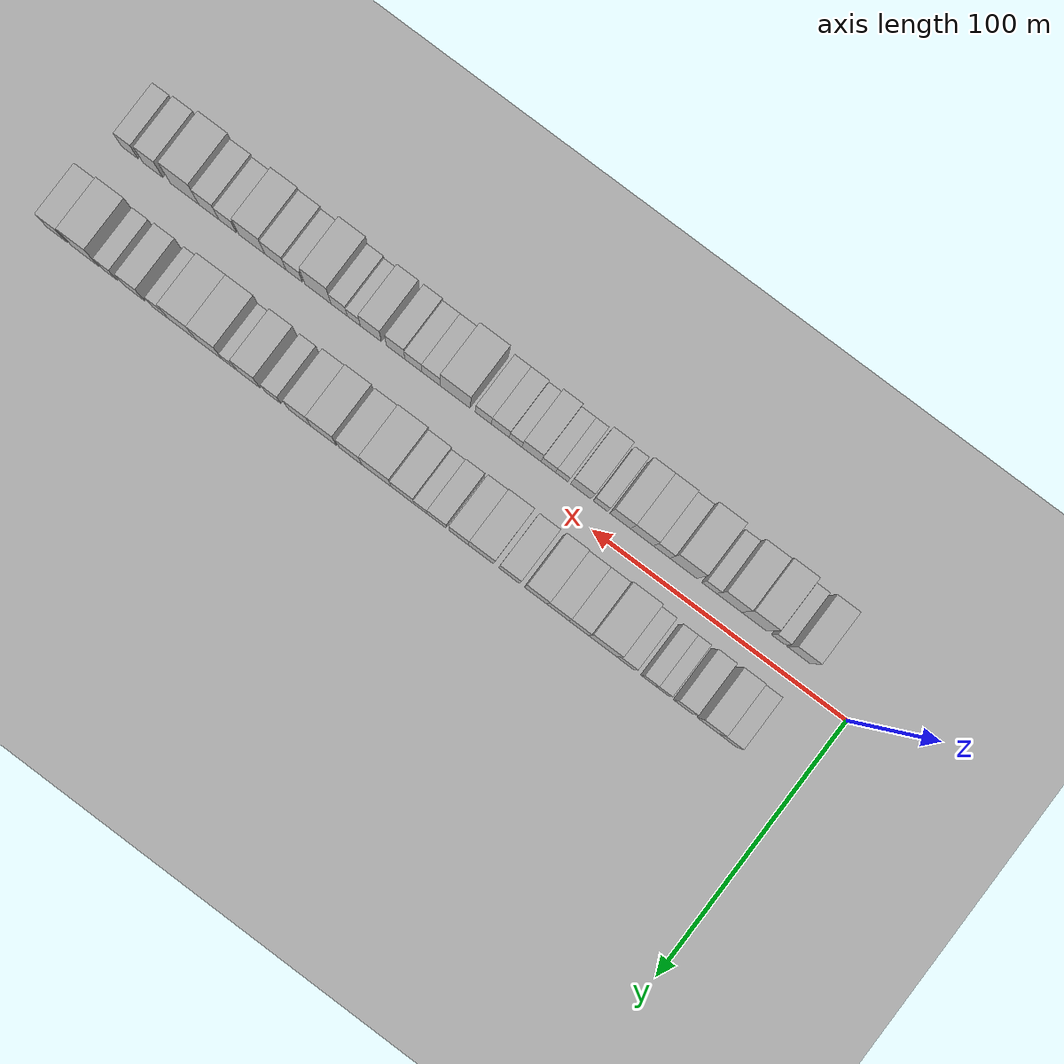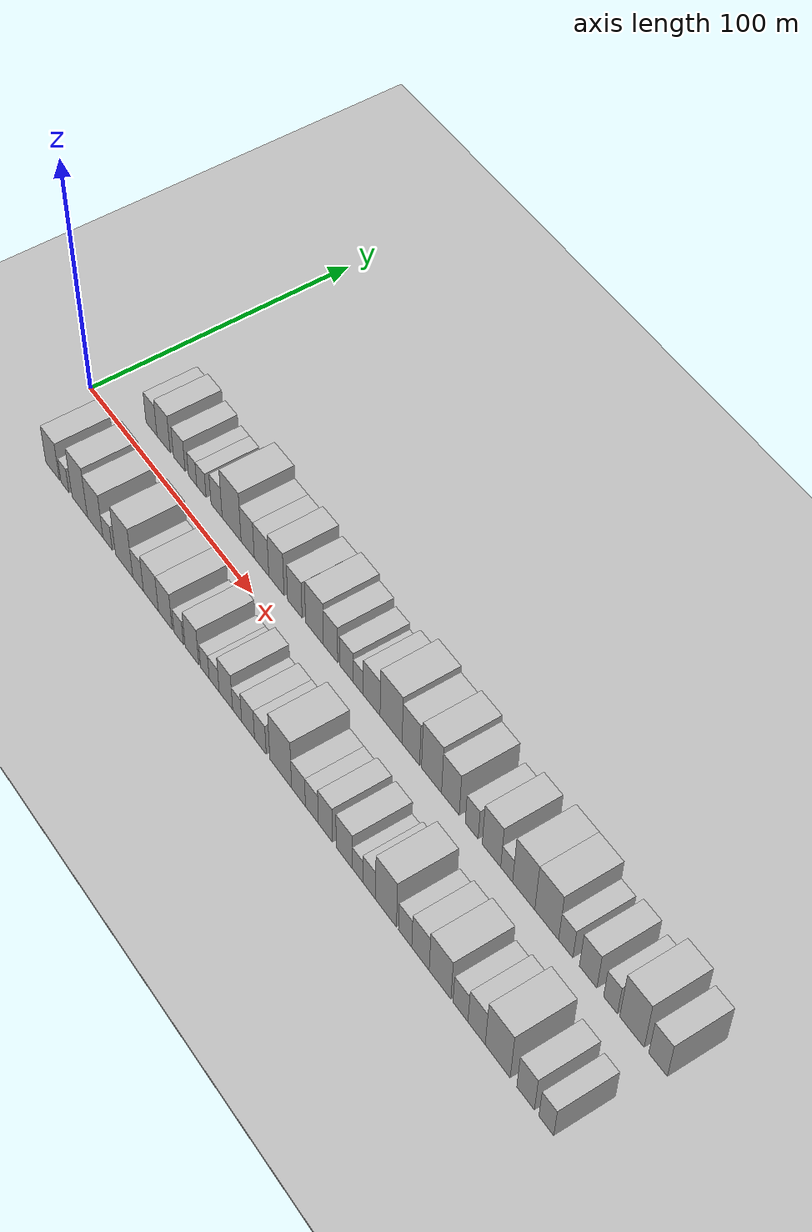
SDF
<?xml version="1.0" encoding="utf-8"?>

<sdf version="1.6">

   <world name="default">

      <gui fullscreen="0">

         <camera name="user_camera">

            <pose>-15 0 4.57585 0 0 0</pose>

            <view_controller>orbit</view_controller>

         </camera>

      </gui>

      <scene>

         <sky>

           <clouds>

             <speed>12</speed>

           </clouds>

         </sky>

         <ambient>0.4 0.4 0.4 1</ambient>

         <background>0.7 0.7 0.7 1</background>

         <shadows>1</shadows>

      </scene>

      <gravity>0 0 -9.8066</gravity>

      <magnetic_field>6e-06 2.3e-05 -4.2e-05</magnetic_field>

      <physics default="0" name="default_physics" type="ode">

         <ode>

            <solver>

               <type>quick</type>

               <iters>10</iters>

               <sor>1.0</sor>

               <use_dynamic_moi_rescaling>0</use_dynamic_moi_rescaling>

            </solver>

            <constraints>

               <cfm>0</cfm>

               <erp>0.2</erp>

               <contact_max_correcting_vel>100</contact_max_correcting_vel>

               <contact_surface_layer>0.001</contact_surface_layer>

            </constraints>

         </ode>

         <max_step_size>0.004</max_step_size>

         <real_time_factor>1</real_time_factor>

         <real_time_update_rate>250</real_time_update_rate>

      </physics>

      <light name="sun" type="directional">

         <cast_shadows>1</cast_shadows>

         <pose>0 0 10 0 0 0</pose>

         <diffuse>0.8 0.8 0.8 1</diffuse>

         <specular>0.2 0.2 0.2 1</specular>

         <attenuation>

            <range>1000</range>

            <constant>0.9</constant>

            <linear>0.01</linear>

            <quadratic>0.001</quadratic>

         </attenuation>

         <direction>-0.5 0.1 -0.9</direction>

      </light>

      <include>

         <name>ground_plane_1</name>

         <uri>model://HANNAS_ground_plane</uri>

         <pose>0 0 0  0 0 0</pose>

      </include>

      <include>

         <name>ground_plane_2</name>

         <uri>model://HANNAS_ground_plane</uri>

         <pose>100 0 0  0 0 0</pose>

      </include>

      <model name="building_1">

         <static>1</static>

         <pose frame="">26.4708 17.5000 0 0.000000 0.000000 1.570796</pose>

         <link name="link">

            <pose frame="">0 0 7.50 0 0 0</pose>

            <collision name="collision">

               <geometry>

                  <box>

                     <size>20.0000 6.9415 15.0000</size>

                  </box>

               </geometry>

               <max_contacts>10</max_contacts>

               <surface>

                  <contact>

                     <ode/>

                  </contact>

                  <bounce/>

                  <friction>

                     <torsional>

                        <ode/>

                     </torsional>

                     <ode/>

                  </friction>

               </surface>

            </collision>

            <visual name="visual">

               <cast_shadows>0</cast_shadows>

               <geometry>

                  <box>

                     <size>20.0000 6.9415 15.0000</size>

                  </box>

               </geometry>

               <material>

                  <script>

                     <uri>model://HANNAS_wall/materials/scripts</uri>

                     <uri>model://HANNAS_wall/materials/textures</uri>

                     <name>vrc/HANNAS_wall</name>

                  </script>

               </material>

            </visual>

            <self_collide>0</self_collide>

            <enable_wind>0</enable_wind>

            <kinematic>0</kinematic>

         </link>

      </model>

      <model name="building_2">

         <static>1</static>

         <pose frame="">34.1181 17.5000 0 0.000000 0.000000 1.570796</pose>

         <link name="link">

            <pose frame="">0 0 9.00 0 0 0</pose>

            <collision name="collision">

               <geometry>

                  <box>

                     <size>20.0000 8.3533 18.0000</size>

                  </box>

               </geometry>

               <max_contacts>10</max_contacts>

               <surface>

                  <contact>

                     <ode/>

                  </contact>

                  <bounce/>

                  <friction>

                     <torsional>

                        <ode/>

                     </torsional>

                     <ode/>

                  </friction>

               </surface>

            </collision>

            <visual name="visual">

               <cast_shadows>0</cast_shadows>

               <geometry>

                  <box>

                     <size>20.0000 8.3533 18.0000</size>

                  </box>

               </geometry>

               <material>

                  <script>

                     <uri>model://HANNAS_wall/materials/scripts</uri>

                     <uri>model://HANNAS_wall/materials/textures</uri>

                     <name>vrc/HANNAS_wall</name>

                  </script>

               </material>

            </visual>

            <self_collide>0</self_collide>

            <enable_wind>0</enable_wind>

            <kinematic>0</kinematic>

         </link>

      </model>

      <model name="building_3">

         <static>1</static>

         <pose frame="">43.9311 17.5000 0 0.000000 0.000000 1.570796</pose>

         <link name="link">

            <pose frame="">0 0 7.50 0 0 0</pose>

            <collision name="collision">

               <geometry>

                  <box>

                     <size>20.0000 7.2727 15.0000</size>

                  </box>

               </geometry>

               <max_contacts>10</max_contacts>

               <surface>

                  <contact>

                     <ode/>

                  </contact>

                  <bounce/>

                  <friction>

                     <torsional>

                        <ode/>

                     </torsional>

                     <ode/>

                  </friction>

               </surface>

            </collision>

            <visual name="visual">

               <cast_shadows>0</cast_shadows>

               <geometry>

                  <box>

                     <size>20.0000 7.2727 15.0000</size>

                  </box>

               </geometry>

               <material>

                  <script>

                     <uri>model://HANNAS_wall/materials/scripts</uri>

                     <uri>model://HANNAS_wall/materials/textures</uri>

                     <name>vrc/HANNAS_wall</name>

                  </script>

               </material>

            </visual>

            <self_collide>0</self_collide>

            <enable_wind>0</enable_wind>

            <kinematic>0</kinematic>

         </link>

      </model>

      <model name="building_4">

         <static>1</static>

         <pose frame="">52.1233 17.5000 0 0.000000 0.000000 1.570796</pose>

         <link name="link">

            <pose frame="">0 0 6.00 0 0 0</pose>

            <collision name="collision">

               <geometry>

                  <box>

                     <size>20.0000 5.1117 12.0000</size>

                  </box>

               </geometry>

               <max_contacts>10</max_contacts>

               <surface>

                  <contact>

                     <ode/>

                  </contact>

                  <bounce/>

                  <friction>

                     <torsional>

                        <ode/>

                     </torsional>

                     <ode/>

                  </friction>

               </surface>

            </collision>

            <visual name="visual">

               <cast_shadows>0</cast_shadows>

               <geometry>

                  <box>

                     <size>20.0000 5.1117 12.0000</size>

                  </box>

               </geometry>

               <material>

                  <script>

                     <uri>model://HANNAS_wall/materials/scripts</uri>

                     <uri>model://HANNAS_wall/materials/textures</uri>

                     <name>vrc/HANNAS_wall</name>

                  </script>

               </material>

            </visual>

            <self_collide>0</self_collide>

            <enable_wind>0</enable_wind>

            <kinematic>0</kinematic>

         </link>

      </model>

      <model name="building_5">

         <static>1</static>

         <pose frame="">57.5063 17.5000 0 0.000000 0.000000 1.570796</pose>

         <link name="link">

            <pose frame="">0 0 6.00 0 0 0</pose>

            <collision name="collision">

               <geometry>

                  <box>

                     <size>20.0000 5.6544 12.0000</size>

                  </box>

               </geometry>

               <max_contacts>10</max_contacts>

               <surface>

                  <contact>

                     <ode/>

                  </contact>

                  <bounce/>

                  <friction>

                     <torsional>

                        <ode/>

                     </torsional>

                     <ode/>

                  </friction>

               </surface>

            </collision>

            <visual name="visual">

               <cast_shadows>0</cast_shadows>

               <geometry>

                  <box>

                     <size>20.0000 5.6544 12.0000</size>

                  </box>

               </geometry>

               <material>

                  <script>

                     <uri>model://HANNAS_wall/materials/scripts</uri>

                     <uri>model://HANNAS_wall/materials/textures</uri>

                     <name>vrc/HANNAS_wall</name>

                  </script>

               </material>

            </visual>

            <self_collide>0</self_collide>

            <enable_wind>0</enable_wind>

            <kinematic>0</kinematic>

         </link>

      </model>

      <model name="building_6">

         <static>1</static>

         <pose frame="">66.6913 17.5000 0 0.000000 0.000000 1.570796</pose>

         <link name="link">

            <pose frame="">0 0 7.50 0 0 0</pose>

            <collision name="collision">

               <geometry>

                  <box>

                     <size>20.0000 6.7156 15.0000</size>

                  </box>

               </geometry>

               <max_contacts>10</max_contacts>

               <surface>

                  <contact>

                     <ode/>

                  </contact>

                  <bounce/>

                  <friction>

                     <torsional>

                        <ode/>

                     </torsional>

                     <ode/>

                  </friction>

               </surface>

            </collision>

            <visual name="visual">

               <cast_shadows>0</cast_shadows>

               <geometry>

                  <box>

                     <size>20.0000 6.7156 15.0000</size>

                  </box>

               </geometry>

               <material>

                  <script>

                     <uri>model://HANNAS_wall/materials/scripts</uri>

                     <uri>model://HANNAS_wall/materials/textures</uri>

                     <name>vrc/HANNAS_wall</name>

                  </script>

               </material>

            </visual>

            <self_collide>0</self_collide>

            <enable_wind>0</enable_wind>

            <kinematic>0</kinematic>

         </link>

      </model>

      <model name="building_7">

         <static>1</static>

         <pose frame="">75.6834 17.5000 0 0.000000 0.000000 1.570796</pose>

         <link name="link">

            <pose frame="">0 0 12.00 0 0 0</pose>

            <collision name="collision">

               <geometry>

                  <box>

                     <size>20.0000 11.2687 24.0000</size>

                  </box>

               </geometry>

               <max_contacts>10</max_contacts>

               <surface>

                  <contact>

                     <ode/>

                  </contact>

                  <bounce/>

                  <friction>

                     <torsional>

                        <ode/>

                     </torsional>

                     <ode/>

                  </friction>

               </surface>

            </collision>

            <visual name="visual">

               <cast_shadows>0</cast_shadows>

               <geometry>

                  <box>

                     <size>20.0000 11.2687 24.0000</size>

                  </box>

               </geometry>

               <material>

                  <script>

                     <uri>model://HANNAS_wall/materials/scripts</uri>

                     <uri>model://HANNAS_wall/materials/textures</uri>

                     <name>vrc/HANNAS_wall</name>

                  </script>

               </material>

            </visual>

            <self_collide>0</self_collide>

            <enable_wind>0</enable_wind>

            <kinematic>0</kinematic>

         </link>

      </model>

      <model name="building_8">

         <static>1</static>

         <pose frame="">85.1692 17.5000 0 0.000000 0.000000 1.570796</pose>

         <link name="link">

            <pose frame="">0 0 9.00 0 0 0</pose>

            <collision name="collision">

               <geometry>

                  <box>

                     <size>20.0000 7.7029 18.0000</size>

                  </box>

               </geometry>

               <max_contacts>10</max_contacts>

               <surface>

                  <contact>

                     <ode/>

                  </contact>

                  <bounce/>

                  <friction>

                     <torsional>

                        <ode/>

                     </torsional>

                     <ode/>

                  </friction>

               </surface>

            </collision>

            <visual name="visual">

               <cast_shadows>0</cast_shadows>

               <geometry>

                  <box>

                     <size>20.0000 7.7029 18.0000</size>

                  </box>

               </geometry>

               <material>

                  <script>

                     <uri>model://HANNAS_wall/materials/scripts</uri>

                     <uri>model://HANNAS_wall/materials/textures</uri>

                     <name>vrc/HANNAS_wall</name>

                  </script>

               </material>

            </visual>

            <self_collide>0</self_collide>

            <enable_wind>0</enable_wind>

            <kinematic>0</kinematic>

         </link>

      </model>

      <model name="building_9">

         <static>1</static>

         <pose frame="">93.2389 17.5000 0 0.000000 0.000000 1.570796</pose>

         <link name="link">

            <pose frame="">0 0 9.00 0 0 0</pose>

            <collision name="collision">

               <geometry>

                  <box>

                     <size>20.0000 8.4366 18.0000</size>

                  </box>

               </geometry>

               <max_contacts>10</max_contacts>

               <surface>

                  <contact>

                     <ode/>

                  </contact>

                  <bounce/>

                  <friction>

                     <torsional>

                        <ode/>

                     </torsional>

                     <ode/>

                  </friction>

               </surface>

            </collision>

            <visual name="visual">

               <cast_shadows>0</cast_shadows>

               <geometry>

                  <box>

                     <size>20.0000 8.4366 18.0000</size>

                  </box>

               </geometry>

               <material>

                  <script>

                     <uri>model://HANNAS_wall/materials/scripts</uri>

                     <uri>model://HANNAS_wall/materials/textures</uri>

                     <name>vrc/HANNAS_wall</name>

                  </script>

               </material>

            </visual>

            <self_collide>0</self_collide>

            <enable_wind>0</enable_wind>

            <kinematic>0</kinematic>

         </link>

      </model>

      <model name="building_10">

         <static>1</static>

         <pose frame="">101.8389 17.5000 0 0.000000 0.000000 1.570796</pose>

         <link name="link">

            <pose frame="">0 0 10.50 0 0 0</pose>

            <collision name="collision">

               <geometry>

                  <box>

                     <size>20.0000 8.7634 21.0000</size>

                  </box>

               </geometry>

               <max_contacts>10</max_contacts>

               <surface>

                  <contact>

                     <ode/>

                  </contact>

                  <bounce/>

                  <friction>

                     <torsional>

                        <ode/>

                     </torsional>

                     <ode/>

                  </friction>

               </surface>

            </collision>

            <visual name="visual">

               <cast_shadows>0</cast_shadows>

               <geometry>

                  <box>

                     <size>20.0000 8.7634 21.0000</size>

                  </box>

               </geometry>

               <material>

                  <script>

                     <uri>model://HANNAS_wall/materials/scripts</uri>

                     <uri>model://HANNAS_wall/materials/textures</uri>

                     <name>vrc/HANNAS_wall</name>

                  </script>

               </material>

            </visual>

            <self_collide>0</self_collide>

            <enable_wind>0</enable_wind>

            <kinematic>0</kinematic>

         </link>

      </model>

      <model name="building_11">

         <static>1</static>

         <pose frame="">112.3076 17.5000 0 0.000000 0.000000 1.570796</pose>

         <link name="link">

            <pose frame="">0 0 9.00 0 0 0</pose>

            <collision name="collision">

               <geometry>

                  <box>

                     <size>20.0000 8.1739 18.0000</size>

                  </box>

               </geometry>

               <max_contacts>10</max_contacts>

               <surface>

                  <contact>

                     <ode/>

                  </contact>

                  <bounce/>

                  <friction>

                     <torsional>

                        <ode/>

                     </torsional>

                     <ode/>

                  </friction>

               </surface>

            </collision>

            <visual name="visual">

               <cast_shadows>0</cast_shadows>

               <geometry>

                  <box>

                     <size>20.0000 8.1739 18.0000</size>

                  </box>

               </geometry>

               <material>

                  <script>

                     <uri>model://HANNAS_wall/materials/scripts</uri>

                     <uri>model://HANNAS_wall/materials/textures</uri>

                     <name>vrc/HANNAS_wall</name>

                  </script>

               </material>

            </visual>

            <self_collide>0</self_collide>

            <enable_wind>0</enable_wind>

            <kinematic>0</kinematic>

         </link>

      </model>

      <model name="building_12">

         <static>1</static>

         <pose frame="">123.3487 17.5000 0 0.000000 0.000000 1.570796</pose>

         <link name="link">

            <pose frame="">0 0 10.50 0 0 0</pose>

            <collision name="collision">

               <geometry>

                  <box>

                     <size>20.0000 9.9083 21.0000</size>

                  </box>

               </geometry>

               <max_contacts>10</max_contacts>

               <surface>

                  <contact>

                     <ode/>

                  </contact>

                  <bounce/>

                  <friction>

                     <torsional>

                        <ode/>

                     </torsional>

                     <ode/>

                  </friction>

               </surface>

            </collision>

            <visual name="visual">

               <cast_shadows>0</cast_shadows>

               <geometry>

                  <box>

                     <size>20.0000 9.9083 21.0000</size>

                  </box>

               </geometry>

               <material>

                  <script>

                     <uri>model://HANNAS_wall/materials/scripts</uri>

                     <uri>model://HANNAS_wall/materials/textures</uri>

                     <name>vrc/HANNAS_wall</name>

                  </script>

               </material>

            </visual>

            <self_collide>0</self_collide>

            <enable_wind>0</enable_wind>

            <kinematic>0</kinematic>

         </link>

      </model>

      <model name="building_13">

         <static>1</static>

         <pose frame="">132.2351 17.5000 0 0.000000 0.000000 1.570796</pose>

         <link name="link">

            <pose frame="">0 0 9.00 0 0 0</pose>

            <collision name="collision">

               <geometry>

                  <box>

                     <size>20.0000 7.8645 18.0000</size>

                  </box>

               </geometry>

               <max_contacts>10</max_contacts>

               <surface>

                  <contact>

                     <ode/>

                  </contact>

                  <bounce/>

                  <friction>

                     <torsional>

                        <ode/>

                     </torsional>

                     <ode/>

                  </friction>

               </surface>

            </collision>

            <visual name="visual">

               <cast_shadows>0</cast_shadows>

               <geometry>

                  <box>

                     <size>20.0000 7.8645 18.0000</size>

                  </box>

               </geometry>

               <material>

                  <script>

                     <uri>model://HANNAS_wall/materials/scripts</uri>

                     <uri>model://HANNAS_wall/materials/textures</uri>

                     <name>vrc/HANNAS_wall</name>

                  </script>

               </material>

            </visual>

            <self_collide>0</self_collide>

            <enable_wind>0</enable_wind>

            <kinematic>0</kinematic>

         </link>

      </model>

      <model name="building_14">

         <static>1</static>

         <pose frame="">140.8836 17.5000 0 0.000000 0.000000 1.570796</pose>

         <link name="link">

            <pose frame="">0 0 7.50 0 0 0</pose>

            <collision name="collision">

               <geometry>

                  <box>

                     <size>20.0000 7.4326 15.0000</size>

                  </box>

               </geometry>

               <max_contacts>10</max_contacts>

               <surface>

                  <contact>

                     <ode/>

                  </contact>

                  <bounce/>

                  <friction>

                     <torsional>

                        <ode/>

                     </torsional>

                     <ode/>

                  </friction>

               </surface>

            </collision>

            <visual name="visual">

               <cast_shadows>0</cast_shadows>

               <geometry>

                  <box>

                     <size>20.0000 7.4326 15.0000</size>

                  </box>

               </geometry>

               <material>

                  <script>

                     <uri>model://HANNAS_wall/materials/scripts</uri>

                     <uri>model://HANNAS_wall/materials/textures</uri>

                     <name>vrc/HANNAS_wall</name>

                  </script>

               </material>

            </visual>

            <self_collide>0</self_collide>

            <enable_wind>0</enable_wind>

            <kinematic>0</kinematic>

         </link>

      </model>

      <model name="building_15">

         <static>1</static>

         <pose frame="">147.3118 17.5000 0 0.000000 0.000000 1.570796</pose>

         <link name="link">

            <pose frame="">0 0 6.00 0 0 0</pose>

            <collision name="collision">

               <geometry>

                  <box>

                     <size>20.0000 5.4236 12.0000</size>

                  </box>

               </geometry>

               <max_contacts>10</max_contacts>

               <surface>

                  <contact>

                     <ode/>

                  </contact>

                  <bounce/>

                  <friction>

                     <torsional>

                        <ode/>

                     </torsional>

                     <ode/>

                  </friction>

               </surface>

            </collision>

            <visual name="visual">

               <cast_shadows>0</cast_shadows>

               <geometry>

                  <box>

                     <size>20.0000 5.4236 12.0000</size>

                  </box>

               </geometry>

               <material>

                  <script>

                     <uri>model://HANNAS_wall/materials/scripts</uri>

                     <uri>model://HANNAS_wall/materials/textures</uri>

                     <name>vrc/HANNAS_wall</name>

                  </script>

               </material>

            </visual>

            <self_collide>0</self_collide>

            <enable_wind>0</enable_wind>

            <kinematic>0</kinematic>

         </link>

      </model>

      <model name="building_16">

         <static>1</static>

         <pose frame="">154.4905 17.5000 0 0.000000 0.000000 1.570796</pose>

         <link name="link">

            <pose frame="">0 0 9.00 0 0 0</pose>

            <collision name="collision">

               <geometry>

                  <box>

                     <size>20.0000 8.9338 18.0000</size>

                  </box>

               </geometry>

               <max_contacts>10</max_contacts>

               <surface>

                  <contact>

                     <ode/>

                  </contact>

                  <bounce/>

                  <friction>

                     <torsional>

                        <ode/>

                     </torsional>

                     <ode/>

                  </friction>

               </surface>

            </collision>

            <visual name="visual">

               <cast_shadows>0</cast_shadows>

               <geometry>

                  <box>

                     <size>20.0000 8.9338 18.0000</size>

                  </box>

               </geometry>

               <material>

                  <script>

                     <uri>model://HANNAS_wall/materials/scripts</uri>

                     <uri>model://HANNAS_wall/materials/textures</uri>

                     <name>vrc/HANNAS_wall</name>

                  </script>

               </material>

            </visual>

            <self_collide>0</self_collide>

            <enable_wind>0</enable_wind>

            <kinematic>0</kinematic>

         </link>

      </model>

      <model name="building_17">

         <static>1</static>

         <pose frame="">164.7405 17.5000 0 0.000000 0.000000 1.570796</pose>

         <link name="link">

            <pose frame="">0 0 12.00 0 0 0</pose>

            <collision name="collision">

               <geometry>

                  <box>

                     <size>20.0000 11.5662 24.0000</size>

                  </box>

               </geometry>

               <max_contacts>10</max_contacts>

               <surface>

                  <contact>

                     <ode/>

                  </contact>

                  <bounce/>

                  <friction>

                     <torsional>

                        <ode/>

                     </torsional>

                     <ode/>

                  </friction>

               </surface>

            </collision>

            <visual name="visual">

               <cast_shadows>0</cast_shadows>

               <geometry>

                  <box>

                     <size>20.0000 11.5662 24.0000</size>

                  </box>

               </geometry>

               <material>

                  <script>

                     <uri>model://HANNAS_wall/materials/scripts</uri>

                     <uri>model://HANNAS_wall/materials/textures</uri>

                     <name>vrc/HANNAS_wall</name>

                  </script>

               </material>

            </visual>

            <self_collide>0</self_collide>

            <enable_wind>0</enable_wind>

            <kinematic>0</kinematic>

         </link>

      </model>

      <model name="building_18">

         <static>1</static>

         <pose frame="">175.0531 17.5000 0 0.000000 0.000000 1.570796</pose>

         <link name="link">

            <pose frame="">0 0 10.50 0 0 0</pose>

            <collision name="collision">

               <geometry>

                  <box>

                     <size>20.0000 9.0590 21.0000</size>

                  </box>

               </geometry>

               <max_contacts>10</max_contacts>

               <surface>

                  <contact>

                     <ode/>

                  </contact>

                  <bounce/>

                  <friction>

                     <torsional>

                        <ode/>

                     </torsional>

                     <ode/>

                  </friction>

               </surface>

            </collision>

            <visual name="visual">

               <cast_shadows>0</cast_shadows>

               <geometry>

                  <box>

                     <size>20.0000 9.0590 21.0000</size>

                  </box>

               </geometry>

               <material>

                  <script>

                     <uri>model://HANNAS_wall/materials/scripts</uri>

                     <uri>model://HANNAS_wall/materials/textures</uri>

                     <name>vrc/HANNAS_wall</name>

                  </script>

               </material>

            </visual>

            <self_collide>0</self_collide>

            <enable_wind>0</enable_wind>

            <kinematic>0</kinematic>

         </link>

      </model>

      <model name="building_19">

         <static>1</static>

         <pose frame="">185.6934 17.5000 0 0.000000 0.000000 1.570796</pose>

         <link name="link">

            <pose frame="">0 0 12.00 0 0 0</pose>

            <collision name="collision">

               <geometry>

                  <box>

                     <size>20.0000 10.2216 24.0000</size>

                  </box>

               </geometry>

               <max_contacts>10</max_contacts>

               <surface>

                  <contact>

                     <ode/>

                  </contact>

                  <bounce/>

                  <friction>

                     <torsional>

                        <ode/>

                     </torsional>

                     <ode/>

                  </friction>

               </surface>

            </collision>

            <visual name="visual">

               <cast_shadows>0</cast_shadows>

               <geometry>

                  <box>

                     <size>20.0000 10.2216 24.0000</size>

                  </box>

               </geometry>

               <material>

                  <script>

                     <uri>model://HANNAS_wall/materials/scripts</uri>

                     <uri>model://HANNAS_wall/materials/textures</uri>

                     <name>vrc/HANNAS_wall</name>

                  </script>

               </material>

            </visual>

            <self_collide>0</self_collide>

            <enable_wind>0</enable_wind>

            <kinematic>0</kinematic>

         </link>

      </model>

      <model name="building_20">

         <static>1</static>

         <pose frame="">195.2485 17.5000 0 0.000000 0.000000 1.570796</pose>

         <link name="link">

            <pose frame="">0 0 10.50 0 0 0</pose>

            <collision name="collision">

               <geometry>

                  <box>

                     <size>20.0000 8.8885 21.0000</size>

                  </box>

               </geometry>

               <max_contacts>10</max_contacts>

               <surface>

                  <contact>

                     <ode/>

                  </contact>

                  <bounce/>

                  <friction>

                     <torsional>

                        <ode/>

                     </torsional>

                     <ode/>

                  </friction>

               </surface>

            </collision>

            <visual name="visual">

               <cast_shadows>0</cast_shadows>

               <geometry>

                  <box>

                     <size>20.0000 8.8885 21.0000</size>

                  </box>

               </geometry>

               <material>

                  <script>

                     <uri>model://HANNAS_wall/materials/scripts</uri>

                     <uri>model://HANNAS_wall/materials/textures</uri>

                     <name>vrc/HANNAS_wall</name>

                  </script>

               </material>

            </visual>

            <self_collide>0</self_collide>

            <enable_wind>0</enable_wind>

            <kinematic>0</kinematic>

         </link>

      </model>

      <model name="building_21">

         <static>1</static>

         <pose frame="">205.8795 17.5000 0 0.000000 0.000000 1.570796</pose>

         <link name="link">

            <pose frame="">0 0 7.50 0 0 0</pose>

            <collision name="collision">

               <geometry>

                  <box>

                     <size>20.0000 6.3734 15.0000</size>

                  </box>

               </geometry>

               <max_contacts>10</max_contacts>

               <surface>

                  <contact>

                     <ode/>

                  </contact>

                  <bounce/>

                  <friction>

                     <torsional>

                        <ode/>

                     </torsional>

                     <ode/>

                  </friction>

               </surface>

            </collision>

            <visual name="visual">

               <cast_shadows>0</cast_shadows>

               <geometry>

                  <box>

                     <size>20.0000 6.3734 15.0000</size>

                  </box>

               </geometry>

               <material>

                  <script>

                     <uri>model://HANNAS_wall/materials/scripts</uri>

                     <uri>model://HANNAS_wall/materials/textures</uri>

                     <name>vrc/HANNAS_wall</name>

                  </script>

               </material>

            </visual>

            <self_collide>0</self_collide>

            <enable_wind>0</enable_wind>

            <kinematic>0</kinematic>

         </link>

      </model>

      <model name="building_22">

         <static>1</static>

         <pose frame="">215.5824 17.5000 0 0.000000 0.000000 1.570796</pose>

         <link name="link">

            <pose frame="">0 0 10.50 0 0 0</pose>

            <collision name="collision">

               <geometry>

                  <box>

                     <size>20.0000 9.0325 21.0000</size>

                  </box>

               </geometry>

               <max_contacts>10</max_contacts>

               <surface>

                  <contact>

                     <ode/>

                  </contact>

                  <bounce/>

                  <friction>

                     <torsional>

                        <ode/>

                     </torsional>

                     <ode/>

                  </friction>

               </surface>

            </collision>

            <visual name="visual">

               <cast_shadows>0</cast_shadows>

               <geometry>

                  <box>

                     <size>20.0000 9.0325 21.0000</size>

                  </box>

               </geometry>

               <material>

                  <script>

                     <uri>model://HANNAS_wall/materials/scripts</uri>

                     <uri>model://HANNAS_wall/materials/textures</uri>

                     <name>vrc/HANNAS_wall</name>

                  </script>

               </material>

            </visual>

            <self_collide>0</self_collide>

            <enable_wind>0</enable_wind>

            <kinematic>0</kinematic>

         </link>

      </model>

      <model name="building_23">

         <static>1</static>

         <pose frame="">222.9593 17.5000 0 0.000000 0.000000 1.570796</pose>

         <link name="link">

            <pose frame="">0 0 6.00 0 0 0</pose>

            <collision name="collision">

               <geometry>

                  <box>

                     <size>20.0000 5.7213 12.0000</size>

                  </box>

               </geometry>

               <max_contacts>10</max_contacts>

               <surface>

                  <contact>

                     <ode/>

                  </contact>

                  <bounce/>

                  <friction>

                     <torsional>

                        <ode/>

                     </torsional>

                     <ode/>

                  </friction>

               </surface>

            </collision>

            <visual name="visual">

               <cast_shadows>0</cast_shadows>

               <geometry>

                  <box>

                     <size>20.0000 5.7213 12.0000</size>

                  </box>

               </geometry>

               <material>

                  <script>

                     <uri>model://HANNAS_wall/materials/scripts</uri>

                     <uri>model://HANNAS_wall/materials/textures</uri>

                     <name>vrc/HANNAS_wall</name>

                  </script>

               </material>

            </visual>

            <self_collide>0</self_collide>

            <enable_wind>0</enable_wind>

            <kinematic>0</kinematic>

         </link>

      </model>

      <model name="building_24">

         <static>1</static>

         <pose frame="">231.1125 17.5000 0 0.000000 0.000000 1.570796</pose>

         <link name="link">

            <pose frame="">0 0 12.00 0 0 0</pose>

            <collision name="collision">

               <geometry>

                  <box>

                     <size>20.0000 10.5853 24.0000</size>

                  </box>

               </geometry>

               <max_contacts>10</max_contacts>

               <surface>

                  <contact>

                     <ode/>

                  </contact>

                  <bounce/>

                  <friction>

                     <torsional>

                        <ode/>

                     </torsional>

                     <ode/>

                  </friction>

               </surface>

            </collision>

            <visual name="visual">

               <cast_shadows>0</cast_shadows>

               <geometry>

                  <box>

                     <size>20.0000 10.5853 24.0000</size>

                  </box>

               </geometry>

               <material>

                  <script>

                     <uri>model://HANNAS_wall/materials/scripts</uri>

                     <uri>model://HANNAS_wall/materials/textures</uri>

                     <name>vrc/HANNAS_wall</name>

                  </script>

               </material>

            </visual>

            <self_collide>0</self_collide>

            <enable_wind>0</enable_wind>

            <kinematic>0</kinematic>

         </link>

      </model>

      <model name="building_25">

         <static>1</static>

         <pose frame="">242.0030 17.5000 0 0.000000 0.000000 1.570796</pose>

         <link name="link">

            <pose frame="">0 0 12.00 0 0 0</pose>

            <collision name="collision">

               <geometry>

                  <box>

                     <size>20.0000 11.1956 24.0000</size>

                  </box>

               </geometry>

               <max_contacts>10</max_contacts>

               <surface>

                  <contact>

                     <ode/>

                  </contact>

                  <bounce/>

                  <friction>

                     <torsional>

                        <ode/>

                     </torsional>

                     <ode/>

                  </friction>

               </surface>

            </collision>

            <visual name="visual">

               <cast_shadows>0</cast_shadows>

               <geometry>

                  <box>

                     <size>20.0000 11.1956 24.0000</size>

                  </box>

               </geometry>

               <material>

                  <script>

                     <uri>model://HANNAS_wall/materials/scripts</uri>

                     <uri>model://HANNAS_wall/materials/textures</uri>

                     <name>vrc/HANNAS_wall</name>

                  </script>

               </material>

            </visual>

            <self_collide>0</self_collide>

            <enable_wind>0</enable_wind>

            <kinematic>0</kinematic>

         </link>

      </model>

      <model name="building_26">

         <static>1</static>

         <pose frame="">250.9000 17.5000 0 0.000000 0.000000 1.570796</pose>

         <link name="link">

            <pose frame="">0 0 7.50 0 0 0</pose>

            <collision name="collision">

               <geometry>

                  <box>

                     <size>20.0000 6.5985 15.0000</size>

                  </box>

               </geometry>

               <max_contacts>10</max_contacts>

               <surface>

                  <contact>

                     <ode/>

                  </contact>

                  <bounce/>

                  <friction>

                     <torsional>

                        <ode/>

                     </torsional>

                     <ode/>

                  </friction>

               </surface>

            </collision>

            <visual name="visual">

               <cast_shadows>0</cast_shadows>

               <geometry>

                  <box>

                     <size>20.0000 6.5985 15.0000</size>

                  </box>

               </geometry>

               <material>

                  <script>

                     <uri>model://HANNAS_wall/materials/scripts</uri>

                     <uri>model://HANNAS_wall/materials/textures</uri>

                     <name>vrc/HANNAS_wall</name>

                  </script>

               </material>

            </visual>

            <self_collide>0</self_collide>

            <enable_wind>0</enable_wind>

            <kinematic>0</kinematic>

         </link>

      </model>

      <model name="building_27">

         <static>1</static>

         <pose frame="">261.1940 17.5000 0 0.000000 0.000000 1.570796</pose>

         <link name="link">

            <pose frame="">0 0 9.00 0 0 0</pose>

            <collision name="collision">

               <geometry>

                  <box>

                     <size>20.0000 7.9895 18.0000</size>

                  </box>

               </geometry>

               <max_contacts>10</max_contacts>

               <surface>

                  <contact>

                     <ode/>

                  </contact>

                  <bounce/>

                  <friction>

                     <torsional>

                        <ode/>

                     </torsional>

                     <ode/>

                  </friction>

               </surface>

            </collision>

            <visual name="visual">

               <cast_shadows>0</cast_shadows>

               <geometry>

                  <box>

                     <size>20.0000 7.9895 18.0000</size>

                  </box>

               </geometry>

               <material>

                  <script>

                     <uri>model://HANNAS_wall/materials/scripts</uri>

                     <uri>model://HANNAS_wall/materials/textures</uri>

                     <name>vrc/HANNAS_wall</name>

                  </script>

               </material>

            </visual>

            <self_collide>0</self_collide>

            <enable_wind>0</enable_wind>

            <kinematic>0</kinematic>

         </link>

      </model>

      <model name="building_28">

         <static>1</static>

         <pose frame="">271.3050 17.5000 0 0.000000 0.000000 1.570796</pose>

         <link name="link">

            <pose frame="">0 0 7.50 0 0 0</pose>

            <collision name="collision">

               <geometry>

                  <box>

                     <size>20.0000 6.2325 15.0000</size>

                  </box>

               </geometry>

               <max_contacts>10</max_contacts>

               <surface>

                  <contact>

                     <ode/>

                  </contact>

                  <bounce/>

                  <friction>

                     <torsional>

                        <ode/>

                     </torsional>

                     <ode/>

                  </friction>

               </surface>

            </collision>

            <visual name="visual">

               <cast_shadows>0</cast_shadows>

               <geometry>

                  <box>

                     <size>20.0000 6.2325 15.0000</size>

                  </box>

               </geometry>

               <material>

                  <script>

                     <uri>model://HANNAS_wall/materials/scripts</uri>

                     <uri>model://HANNAS_wall/materials/textures</uri>

                     <name>vrc/HANNAS_wall</name>

                  </script>

               </material>

            </visual>

            <self_collide>0</self_collide>

            <enable_wind>0</enable_wind>

            <kinematic>0</kinematic>

         </link>

      </model>

      <model name="building_29">

         <static>1</static>

         <pose frame="">280.8376 17.5000 0 0.000000 0.000000 1.570796</pose>

         <link name="link">

            <pose frame="">0 0 12.00 0 0 0</pose>

            <collision name="collision">

               <geometry>

                  <box>

                     <size>20.0000 10.8327 24.0000</size>

                  </box>

               </geometry>

               <max_contacts>10</max_contacts>

               <surface>

                  <contact>

                     <ode/>

                  </contact>

                  <bounce/>

                  <friction>

                     <torsional>

                        <ode/>

                     </torsional>

                     <ode/>

                  </friction>

               </surface>

            </collision>

            <visual name="visual">

               <cast_shadows>0</cast_shadows>

               <geometry>

                  <box>

                     <size>20.0000 10.8327 24.0000</size>

                  </box>

               </geometry>

               <material>

                  <script>

                     <uri>model://HANNAS_wall/materials/scripts</uri>

                     <uri>model://HANNAS_wall/materials/textures</uri>

                     <name>vrc/HANNAS_wall</name>

                  </script>

               </material>

            </visual>

            <self_collide>0</self_collide>

            <enable_wind>0</enable_wind>

            <kinematic>0</kinematic>

         </link>

      </model>

      <model name="building_30">

         <static>1</static>

         <pose frame="">292.2937 17.5000 0 0.000000 0.000000 1.570796</pose>

         <link name="link">

            <pose frame="">0 0 9.00 0 0 0</pose>

            <collision name="collision">

               <geometry>

                  <box>

                     <size>20.0000 8.0795 18.0000</size>

                  </box>

               </geometry>

               <max_contacts>10</max_contacts>

               <surface>

                  <contact>

                     <ode/>

                  </contact>

                  <bounce/>

                  <friction>

                     <torsional>

                        <ode/>

                     </torsional>

                     <ode/>

                  </friction>

               </surface>

            </collision>

            <visual name="visual">

               <cast_shadows>0</cast_shadows>

               <geometry>

                  <box>

                     <size>20.0000 8.0795 18.0000</size>

                  </box>

               </geometry>

               <material>

                  <script>

                     <uri>model://HANNAS_wall/materials/scripts</uri>

                     <uri>model://HANNAS_wall/materials/textures</uri>

                     <name>vrc/HANNAS_wall</name>

                  </script>

               </material>

            </visual>

            <self_collide>0</self_collide>

            <enable_wind>0</enable_wind>

            <kinematic>0</kinematic>

         </link>

      </model>

      <model name="building_31">

         <static>1</static>

         <pose frame="">24.4698 -17.5000 0 0.000000 0.000000 1.570796</pose>

         <link name="link">

            <pose frame="">0 0 9.00 0 0 0</pose>

            <collision name="collision">

               <geometry>

                  <box>

                     <size>20.0000 8.9396 18.0000</size>

                  </box>

               </geometry>

               <max_contacts>10</max_contacts>

               <surface>

                  <contact>

                     <ode/>

                  </contact>

                  <bounce/>

                  <friction>

                     <torsional>

                        <ode/>

                     </torsional>

                     <ode/>

                  </friction>

               </surface>

            </collision>

            <visual name="visual">

               <cast_shadows>0</cast_shadows>

               <geometry>

                  <box>

                     <size>20.0000 8.9396 18.0000</size>

                  </box>

               </geometry>

               <material>

                  <script>

                     <uri>model://HANNAS_wall/materials/scripts</uri>

                     <uri>model://HANNAS_wall/materials/textures</uri>

                     <name>vrc/HANNAS_wall</name>

                  </script>

               </material>

            </visual>

            <self_collide>0</self_collide>

            <enable_wind>0</enable_wind>

            <kinematic>0</kinematic>

         </link>

      </model>

      <model name="building_32">

         <static>1</static>

         <pose frame="">32.5034 -17.5000 0 0.000000 0.000000 1.570796</pose>

         <link name="link">

            <pose frame="">0 0 6.00 0 0 0</pose>

            <collision name="collision">

               <geometry>

                  <box>

                     <size>20.0000 5.1276 12.0000</size>

                  </box>

               </geometry>

               <max_contacts>10</max_contacts>

               <surface>

                  <contact>

                     <ode/>

                  </contact>

                  <bounce/>

                  <friction>

                     <torsional>

                        <ode/>

                     </torsional>

                     <ode/>

                  </friction>

               </surface>

            </collision>

            <visual name="visual">

               <cast_shadows>0</cast_shadows>

               <geometry>

                  <box>

                     <size>20.0000 5.1276 12.0000</size>

                  </box>

               </geometry>

               <material>

                  <script>

                     <uri>model://HANNAS_wall/materials/scripts</uri>

                     <uri>model://HANNAS_wall/materials/textures</uri>

                     <name>vrc/HANNAS_wall</name>

                  </script>

               </material>

            </visual>

            <self_collide>0</self_collide>

            <enable_wind>0</enable_wind>

            <kinematic>0</kinematic>

         </link>

      </model>

      <model name="building_33">

         <static>1</static>

         <pose frame="">41.9767 -17.5000 0 0.000000 0.000000 1.570796</pose>

         <link name="link">

            <pose frame="">0 0 12.00 0 0 0</pose>

            <collision name="collision">

               <geometry>

                  <box>

                     <size>20.0000 9.8190 24.0000</size>

                  </box>

               </geometry>

               <max_contacts>10</max_contacts>

               <surface>

                  <contact>

                     <ode/>

                  </contact>

                  <bounce/>

                  <friction>

                     <torsional>

                        <ode/>

                     </torsional>

                     <ode/>

                  </friction>

               </surface>

            </collision>

            <visual name="visual">

               <cast_shadows>0</cast_shadows>

               <geometry>

                  <box>

                     <size>20.0000 9.8190 24.0000</size>

                  </box>

               </geometry>

               <material>

                  <script>

                     <uri>model://HANNAS_wall/materials/scripts</uri>

                     <uri>model://HANNAS_wall/materials/textures</uri>

                     <name>vrc/HANNAS_wall</name>

                  </script>

               </material>

            </visual>

            <self_collide>0</self_collide>

            <enable_wind>0</enable_wind>

            <kinematic>0</kinematic>

         </link>

      </model>

      <model name="building_34">

         <static>1</static>

         <pose frame="">51.7552 -17.5000 0 0.000000 0.000000 1.570796</pose>

         <link name="link">

            <pose frame="">0 0 10.50 0 0 0</pose>

            <collision name="collision">

               <geometry>

                  <box>

                     <size>20.0000 9.7381 21.0000</size>

                  </box>

               </geometry>

               <max_contacts>10</max_contacts>

               <surface>

                  <contact>

                     <ode/>

                  </contact>

                  <bounce/>

                  <friction>

                     <torsional>

                        <ode/>

                     </torsional>

                     <ode/>

                  </friction>

               </surface>

            </collision>

            <visual name="visual">

               <cast_shadows>0</cast_shadows>

               <geometry>

                  <box>

                     <size>20.0000 9.7381 21.0000</size>

                  </box>

               </geometry>

               <material>

                  <script>

                     <uri>model://HANNAS_wall/materials/scripts</uri>

                     <uri>model://HANNAS_wall/materials/textures</uri>

                     <name>vrc/HANNAS_wall</name>

                  </script>

               </material>

            </visual>

            <self_collide>0</self_collide>

            <enable_wind>0</enable_wind>

            <kinematic>0</kinematic>

         </link>

      </model>

      <model name="building_35">

         <static>1</static>

         <pose frame="">59.5326 -17.5000 0 0.000000 0.000000 1.570796</pose>

         <link name="link">

            <pose frame="">0 0 6.00 0 0 0</pose>

            <collision name="collision">

               <geometry>

                  <box>

                     <size>20.0000 5.8166 12.0000</size>

                  </box>

               </geometry>

               <max_contacts>10</max_contacts>

               <surface>

                  <contact>

                     <ode/>

                  </contact>

                  <bounce/>

                  <friction>

                     <torsional>

                        <ode/>

                     </torsional>

                     <ode/>

                  </friction>

               </surface>

            </collision>

            <visual name="visual">

               <cast_shadows>0</cast_shadows>

               <geometry>

                  <box>

                     <size>20.0000 5.8166 12.0000</size>

                  </box>

               </geometry>

               <material>

                  <script>

                     <uri>model://HANNAS_wall/materials/scripts</uri>

                     <uri>model://HANNAS_wall/materials/textures</uri>

                     <name>vrc/HANNAS_wall</name>

                  </script>

               </material>

            </visual>

            <self_collide>0</self_collide>

            <enable_wind>0</enable_wind>

            <kinematic>0</kinematic>

         </link>

      </model>

      <model name="building_36">

         <static>1</static>

         <pose frame="">69.7482 -17.5000 0 0.000000 0.000000 1.570796</pose>

         <link name="link">

            <pose frame="">0 0 12.00 0 0 0</pose>

            <collision name="collision">

               <geometry>

                  <box>

                     <size>20.0000 10.6147 24.0000</size>

                  </box>

               </geometry>

               <max_contacts>10</max_contacts>

               <surface>

                  <contact>

                     <ode/>

                  </contact>

                  <bounce/>

                  <friction>

                     <torsional>

                        <ode/>

                     </torsional>

                     <ode/>

                  </friction>

               </surface>

            </collision>

            <visual name="visual">

               <cast_shadows>0</cast_shadows>

               <geometry>

                  <box>

                     <size>20.0000 10.6147 24.0000</size>

                  </box>

               </geometry>

               <material>

                  <script>

                     <uri>model://HANNAS_wall/materials/scripts</uri>

                     <uri>model://HANNAS_wall/materials/textures</uri>

                     <name>vrc/HANNAS_wall</name>

                  </script>

               </material>

            </visual>

            <self_collide>0</self_collide>

            <enable_wind>0</enable_wind>

            <kinematic>0</kinematic>

         </link>

      </model>

      <model name="building_37">

         <static>1</static>

         <pose frame="">78.3023 -17.5000 0 0.000000 0.000000 1.570796</pose>

         <link name="link">

            <pose frame="">0 0 7.50 0 0 0</pose>

            <collision name="collision">

               <geometry>

                  <box>

                     <size>20.0000 6.4936 15.0000</size>

                  </box>

               </geometry>

               <max_contacts>10</max_contacts>

               <surface>

                  <contact>

                     <ode/>

                  </contact>

                  <bounce/>

                  <friction>

                     <torsional>

                        <ode/>

                     </torsional>

                     <ode/>

                  </friction>

               </surface>

            </collision>

            <visual name="visual">

               <cast_shadows>0</cast_shadows>

               <geometry>

                  <box>

                     <size>20.0000 6.4936 15.0000</size>

                  </box>

               </geometry>

               <material>

                  <script>

                     <uri>model://HANNAS_wall/materials/scripts</uri>

                     <uri>model://HANNAS_wall/materials/textures</uri>

                     <name>vrc/HANNAS_wall</name>

                  </script>

               </material>

            </visual>

            <self_collide>0</self_collide>

            <enable_wind>0</enable_wind>

            <kinematic>0</kinematic>

         </link>

      </model>

      <model name="building_38">

         <static>1</static>

         <pose frame="">86.0346 -17.5000 0 0.000000 0.000000 1.570796</pose>

         <link name="link">

            <pose frame="">0 0 9.00 0 0 0</pose>

            <collision name="collision">

               <geometry>

                  <box>

                     <size>20.0000 8.9710 18.0000</size>

                  </box>

               </geometry>

               <max_contacts>10</max_contacts>

               <surface>

                  <contact>

                     <ode/>

                  </contact>

                  <bounce/>

                  <friction>

                     <torsional>

                        <ode/>

                     </torsional>

                     <ode/>

                  </friction>

               </surface>

            </collision>

            <visual name="visual">

               <cast_shadows>0</cast_shadows>

               <geometry>

                  <box>

                     <size>20.0000 8.9710 18.0000</size>

                  </box>

               </geometry>

               <material>

                  <script>

                     <uri>model://HANNAS_wall/materials/scripts</uri>

                     <uri>model://HANNAS_wall/materials/textures</uri>

                     <name>vrc/HANNAS_wall</name>

                  </script>

               </material>

            </visual>

            <self_collide>0</self_collide>

            <enable_wind>0</enable_wind>

            <kinematic>0</kinematic>

         </link>

      </model>

      <model name="building_39">

         <static>1</static>

         <pose frame="">94.6018 -17.5000 0 0.000000 0.000000 1.570796</pose>

         <link name="link">

            <pose frame="">0 0 9.00 0 0 0</pose>

            <collision name="collision">

               <geometry>

                  <box>

                     <size>20.0000 8.1634 18.0000</size>

                  </box>

               </geometry>

               <max_contacts>10</max_contacts>

               <surface>

                  <contact>

                     <ode/>

                  </contact>

                  <bounce/>

                  <friction>

                     <torsional>

                        <ode/>

                     </torsional>

                     <ode/>

                  </friction>

               </surface>

            </collision>

            <visual name="visual">

               <cast_shadows>0</cast_shadows>

               <geometry>

                  <box>

                     <size>20.0000 8.1634 18.0000</size>

                  </box>

               </geometry>

               <material>

                  <script>

                     <uri>model://HANNAS_wall/materials/scripts</uri>

                     <uri>model://HANNAS_wall/materials/textures</uri>

                     <name>vrc/HANNAS_wall</name>

                  </script>

               </material>

            </visual>

            <self_collide>0</self_collide>

            <enable_wind>0</enable_wind>

            <kinematic>0</kinematic>

         </link>

      </model>

      <model name="building_40">

         <static>1</static>

         <pose frame="">102.4759 -17.5000 0 0.000000 0.000000 1.570796</pose>

         <link name="link">

            <pose frame="">0 0 6.00 0 0 0</pose>

            <collision name="collision">

               <geometry>

                  <box>

                     <size>20.0000 5.5847 12.0000</size>

                  </box>

               </geometry>

               <max_contacts>10</max_contacts>

               <surface>

                  <contact>

                     <ode/>

                  </contact>

                  <bounce/>

                  <friction>

                     <torsional>

                        <ode/>

                     </torsional>

                     <ode/>

                  </friction>

               </surface>

            </collision>

            <visual name="visual">

               <cast_shadows>0</cast_shadows>

               <geometry>

                  <box>

                     <size>20.0000 5.5847 12.0000</size>

                  </box>

               </geometry>

               <material>

                  <script>

                     <uri>model://HANNAS_wall/materials/scripts</uri>

                     <uri>model://HANNAS_wall/materials/textures</uri>

                     <name>vrc/HANNAS_wall</name>

                  </script>

               </material>

            </visual>

            <self_collide>0</self_collide>

            <enable_wind>0</enable_wind>

            <kinematic>0</kinematic>

         </link>

      </model>

      <model name="building_41">

         <static>1</static>

         <pose frame="">110.2476 -17.5000 0 0.000000 0.000000 1.570796</pose>

         <link name="link">

            <pose frame="">0 0 9.00 0 0 0</pose>

            <collision name="collision">

               <geometry>

                  <box>

                     <size>20.0000 7.9588 18.0000</size>

                  </box>

               </geometry>

               <max_contacts>10</max_contacts>

               <surface>

                  <contact>

                     <ode/>

                  </contact>

                  <bounce/>

                  <friction>

                     <torsional>

                        <ode/>

                     </torsional>

                     <ode/>

                  </friction>

               </surface>

            </collision>

            <visual name="visual">

               <cast_shadows>0</cast_shadows>

               <geometry>

                  <box>

                     <size>20.0000 7.9588 18.0000</size>

                  </box>

               </geometry>

               <material>

                  <script>

                     <uri>model://HANNAS_wall/materials/scripts</uri>

                     <uri>model://HANNAS_wall/materials/textures</uri>

                     <name>vrc/HANNAS_wall</name>

                  </script>

               </material>

            </visual>

            <self_collide>0</self_collide>

            <enable_wind>0</enable_wind>

            <kinematic>0</kinematic>

         </link>

      </model>

      <model name="building_42">

         <static>1</static>

         <pose frame="">117.7077 -17.5000 0 0.000000 0.000000 1.570796</pose>

         <link name="link">

            <pose frame="">0 0 6.00 0 0 0</pose>

            <collision name="collision">

               <geometry>

                  <box>

                     <size>20.0000 4.9614 12.0000</size>

                  </box>

               </geometry>

               <max_contacts>10</max_contacts>

               <surface>

                  <contact>

                     <ode/>

                  </contact>

                  <bounce/>

                  <friction>

                     <torsional>

                        <ode/>

                     </torsional>

                     <ode/>

                  </friction>

               </surface>

            </collision>

            <visual name="visual">

               <cast_shadows>0</cast_shadows>

               <geometry>

                  <box>

                     <size>20.0000 4.9614 12.0000</size>

                  </box>

               </geometry>

               <material>

                  <script>

                     <uri>model://HANNAS_wall/materials/scripts</uri>

                     <uri>model://HANNAS_wall/materials/textures</uri>

                     <name>vrc/HANNAS_wall</name>

                  </script>

               </material>

            </visual>

            <self_collide>0</self_collide>

            <enable_wind>0</enable_wind>

            <kinematic>0</kinematic>

         </link>

      </model>

      <model name="building_43">

         <static>1</static>

         <pose frame="">123.0354 -17.5000 0 0.000000 0.000000 1.570796</pose>

         <link name="link">

            <pose frame="">0 0 6.00 0 0 0</pose>

            <collision name="collision">

               <geometry>

                  <box>

                     <size>20.0000 5.6939 12.0000</size>

                  </box>

               </geometry>

               <max_contacts>10</max_contacts>

               <surface>

                  <contact>

                     <ode/>

                  </contact>

                  <bounce/>

                  <friction>

                     <torsional>

                        <ode/>

                     </torsional>

                     <ode/>

                  </friction>

               </surface>

            </collision>

            <visual name="visual">

               <cast_shadows>0</cast_shadows>

               <geometry>

                  <box>

                     <size>20.0000 5.6939 12.0000</size>

                  </box>

               </geometry>

               <material>

                  <script>

                     <uri>model://HANNAS_wall/materials/scripts</uri>

                     <uri>model://HANNAS_wall/materials/textures</uri>

                     <name>vrc/HANNAS_wall</name>

                  </script>

               </material>

            </visual>

            <self_collide>0</self_collide>

            <enable_wind>0</enable_wind>

            <kinematic>0</kinematic>

         </link>

      </model>

      <model name="building_44">

         <static>1</static>

         <pose frame="">129.6922 -17.5000 0 0.000000 0.000000 1.570796</pose>

         <link name="link">

            <pose frame="">0 0 9.00 0 0 0</pose>

            <collision name="collision">

               <geometry>

                  <box>

                     <size>20.0000 7.6197 18.0000</size>

                  </box>

               </geometry>

               <max_contacts>10</max_contacts>

               <surface>

                  <contact>

                     <ode/>

                  </contact>

                  <bounce/>

                  <friction>

                     <torsional>

                        <ode/>

                     </torsional>

                     <ode/>

                  </friction>

               </surface>

            </collision>

            <visual name="visual">

               <cast_shadows>0</cast_shadows>

               <geometry>

                  <box>

                     <size>20.0000 7.6197 18.0000</size>

                  </box>

               </geometry>

               <material>

                  <script>

                     <uri>model://HANNAS_wall/materials/scripts</uri>

                     <uri>model://HANNAS_wall/materials/textures</uri>

                     <name>vrc/HANNAS_wall</name>

                  </script>

               </material>

            </visual>

            <self_collide>0</self_collide>

            <enable_wind>0</enable_wind>

            <kinematic>0</kinematic>

         </link>

      </model>

      <model name="building_45">

         <static>1</static>

         <pose frame="">136.0323 -17.5000 0 0.000000 0.000000 1.570796</pose>

         <link name="link">

            <pose frame="">0 0 6.00 0 0 0</pose>

            <collision name="collision">

               <geometry>

                  <box>

                     <size>20.0000 5.0606 12.0000</size>

                  </box>

               </geometry>

               <max_contacts>10</max_contacts>

               <surface>

                  <contact>

                     <ode/>

                  </contact>

                  <bounce/>

                  <friction>

                     <torsional>

                        <ode/>

                     </torsional>

                     <ode/>

                  </friction>

               </surface>

            </collision>

            <visual name="visual">

               <cast_shadows>0</cast_shadows>

               <geometry>

                  <box>

                     <size>20.0000 5.0606 12.0000</size>

                  </box>

               </geometry>

               <material>

                  <script>

                     <uri>model://HANNAS_wall/materials/scripts</uri>

                     <uri>model://HANNAS_wall/materials/textures</uri>

                     <name>vrc/HANNAS_wall</name>

                  </script>

               </material>

            </visual>

            <self_collide>0</self_collide>

            <enable_wind>0</enable_wind>

            <kinematic>0</kinematic>

         </link>

      </model>

      <model name="building_46">

         <static>1</static>

         <pose frame="">142.1181 -17.5000 0 0.000000 0.000000 1.570796</pose>

         <link name="link">

            <pose frame="">0 0 7.50 0 0 0</pose>

            <collision name="collision">

               <geometry>

                  <box>

                     <size>20.0000 7.1110 15.0000</size>

                  </box>

               </geometry>

               <max_contacts>10</max_contacts>

               <surface>

                  <contact>

                     <ode/>

                  </contact>

                  <bounce/>

                  <friction>

                     <torsional>

                        <ode/>

                     </torsional>

                     <ode/>

                  </friction>

               </surface>

            </collision>

            <visual name="visual">

               <cast_shadows>0</cast_shadows>

               <geometry>

                  <box>

                     <size>20.0000 7.1110 15.0000</size>

                  </box>

               </geometry>

               <material>

                  <script>

                     <uri>model://HANNAS_wall/materials/scripts</uri>

                     <uri>model://HANNAS_wall/materials/textures</uri>

                     <name>vrc/HANNAS_wall</name>

                  </script>

               </material>

            </visual>

            <self_collide>0</self_collide>

            <enable_wind>0</enable_wind>

            <kinematic>0</kinematic>

         </link>

      </model>

      <model name="building_47">

         <static>1</static>

         <pose frame="">148.8772 -17.5000 0 0.000000 0.000000 1.570796</pose>

         <link name="link">

            <pose frame="">0 0 7.50 0 0 0</pose>

            <collision name="collision">

               <geometry>

                  <box>

                     <size>20.0000 6.4071 15.0000</size>

                  </box>

               </geometry>

               <max_contacts>10</max_contacts>

               <surface>

                  <contact>

                     <ode/>

                  </contact>

                  <bounce/>

                  <friction>

                     <torsional>

                        <ode/>

                     </torsional>

                     <ode/>

                  </friction>

               </surface>

            </collision>

            <visual name="visual">

               <cast_shadows>0</cast_shadows>

               <geometry>

                  <box>

                     <size>20.0000 6.4071 15.0000</size>

                  </box>

               </geometry>

               <material>

                  <script>

                     <uri>model://HANNAS_wall/materials/scripts</uri>

                     <uri>model://HANNAS_wall/materials/textures</uri>

                     <name>vrc/HANNAS_wall</name>

                  </script>

               </material>

            </visual>

            <self_collide>0</self_collide>

            <enable_wind>0</enable_wind>

            <kinematic>0</kinematic>

         </link>

      </model>

      <model name="building_48">

         <static>1</static>

         <pose frame="">159.9604 -17.5000 0 0.000000 0.000000 1.570796</pose>

         <link name="link">

            <pose frame="">0 0 12.00 0 0 0</pose>

            <collision name="collision">

               <geometry>

                  <box>

                     <size>20.0000 11.7594 24.0000</size>

                  </box>

               </geometry>

               <max_contacts>10</max_contacts>

               <surface>

                  <contact>

                     <ode/>

                  </contact>

                  <bounce/>

                  <friction>

                     <torsional>

                        <ode/>

                     </torsional>

                     <ode/>

                  </friction>

               </surface>

            </collision>

            <visual name="visual">

               <cast_shadows>0</cast_shadows>

               <geometry>

                  <box>

                     <size>20.0000 11.7594 24.0000</size>

                  </box>

               </geometry>

               <material>

                  <script>

                     <uri>model://HANNAS_wall/materials/scripts</uri>

                     <uri>model://HANNAS_wall/materials/textures</uri>

                     <name>vrc/HANNAS_wall</name>

                  </script>

               </material>

            </visual>

            <self_collide>0</self_collide>

            <enable_wind>0</enable_wind>

            <kinematic>0</kinematic>

         </link>

      </model>

      <model name="building_49">

         <static>1</static>

         <pose frame="">169.5211 -17.5000 0 0.000000 0.000000 1.570796</pose>

         <link name="link">

            <pose frame="">0 0 7.50 0 0 0</pose>

            <collision name="collision">

               <geometry>

                  <box>

                     <size>20.0000 7.3620 15.0000</size>

                  </box>

               </geometry>

               <max_contacts>10</max_contacts>

               <surface>

                  <contact>

                     <ode/>

                  </contact>

                  <bounce/>

                  <friction>

                     <torsional>

                        <ode/>

                     </torsional>

                     <ode/>

                  </friction>

               </surface>

            </collision>

            <visual name="visual">

               <cast_shadows>0</cast_shadows>

               <geometry>

                  <box>

                     <size>20.0000 7.3620 15.0000</size>

                  </box>

               </geometry>

               <material>

                  <script>

                     <uri>model://HANNAS_wall/materials/scripts</uri>

                     <uri>model://HANNAS_wall/materials/textures</uri>

                     <name>vrc/HANNAS_wall</name>

                  </script>

               </material>

            </visual>

            <self_collide>0</self_collide>

            <enable_wind>0</enable_wind>

            <kinematic>0</kinematic>

         </link>

      </model>

      <model name="building_50">

         <static>1</static>

         <pose frame="">176.5949 -17.5000 0 0.000000 0.000000 1.570796</pose>

         <link name="link">

            <pose frame="">0 0 7.50 0 0 0</pose>

            <collision name="collision">

               <geometry>

                  <box>

                     <size>20.0000 6.7854 15.0000</size>

                  </box>

               </geometry>

               <max_contacts>10</max_contacts>

               <surface>

                  <contact>

                     <ode/>

                  </contact>

                  <bounce/>

                  <friction>

                     <torsional>

                        <ode/>

                     </torsional>

                     <ode/>

                  </friction>

               </surface>

            </collision>

            <visual name="visual">

               <cast_shadows>0</cast_shadows>

               <geometry>

                  <box>

                     <size>20.0000 6.7854 15.0000</size>

                  </box>

               </geometry>

               <material>

                  <script>

                     <uri>model://HANNAS_wall/materials/scripts</uri>

                     <uri>model://HANNAS_wall/materials/textures</uri>

                     <name>vrc/HANNAS_wall</name>

                  </script>

               </material>

            </visual>

            <self_collide>0</self_collide>

            <enable_wind>0</enable_wind>

            <kinematic>0</kinematic>

         </link>

      </model>

      <model name="building_51">

         <static>1</static>

         <pose frame="">183.6691 -17.5000 0 0.000000 0.000000 1.570796</pose>

         <link name="link">

            <pose frame="">0 0 9.00 0 0 0</pose>

            <collision name="collision">

               <geometry>

                  <box>

                     <size>20.0000 7.3631 18.0000</size>

                  </box>

               </geometry>

               <max_contacts>10</max_contacts>

               <surface>

                  <contact>

                     <ode/>

                  </contact>

                  <bounce/>

                  <friction>

                     <torsional>

                        <ode/>

                     </torsional>

                     <ode/>

                  </friction>

               </surface>

            </collision>

            <visual name="visual">

               <cast_shadows>0</cast_shadows>

               <geometry>

                  <box>

                     <size>20.0000 7.3631 18.0000</size>

                  </box>

               </geometry>

               <material>

                  <script>

                     <uri>model://HANNAS_wall/materials/scripts</uri>

                     <uri>model://HANNAS_wall/materials/textures</uri>

                     <name>vrc/HANNAS_wall</name>

                  </script>

               </material>

            </visual>

            <self_collide>0</self_collide>

            <enable_wind>0</enable_wind>

            <kinematic>0</kinematic>

         </link>

      </model>

      <model name="building_52">

         <static>1</static>

         <pose frame="">193.5242 -17.5000 0 0.000000 0.000000 1.570796</pose>

         <link name="link">

            <pose frame="">0 0 9.00 0 0 0</pose>

            <collision name="collision">

               <geometry>

                  <box>

                     <size>20.0000 8.3470 18.0000</size>

                  </box>

               </geometry>

               <max_contacts>10</max_contacts>

               <surface>

                  <contact>

                     <ode/>

                  </contact>

                  <bounce/>

                  <friction>

                     <torsional>

                        <ode/>

                     </torsional>

                     <ode/>

                  </friction>

               </surface>

            </collision>

            <visual name="visual">

               <cast_shadows>0</cast_shadows>

               <geometry>

                  <box>

                     <size>20.0000 8.3470 18.0000</size>

                  </box>

               </geometry>

               <material>

                  <script>

                     <uri>model://HANNAS_wall/materials/scripts</uri>

                     <uri>model://HANNAS_wall/materials/textures</uri>

                     <name>vrc/HANNAS_wall</name>

                  </script>

               </material>

            </visual>

            <self_collide>0</self_collide>

            <enable_wind>0</enable_wind>

            <kinematic>0</kinematic>

         </link>

      </model>

      <model name="building_53">

         <static>1</static>

         <pose frame="">200.3309 -17.5000 0 0.000000 0.000000 1.570796</pose>

         <link name="link">

            <pose frame="">0 0 6.00 0 0 0</pose>

            <collision name="collision">

               <geometry>

                  <box>

                     <size>20.0000 5.2664 12.0000</size>

                  </box>

               </geometry>

               <max_contacts>10</max_contacts>

               <surface>

                  <contact>

                     <ode/>

                  </contact>

                  <bounce/>

                  <friction>

                     <torsional>

                        <ode/>

                     </torsional>

                     <ode/>

                  </friction>

               </surface>

            </collision>

            <visual name="visual">

               <cast_shadows>0</cast_shadows>

               <geometry>

                  <box>

                     <size>20.0000 5.2664 12.0000</size>

                  </box>

               </geometry>

               <material>

                  <script>

                     <uri>model://HANNAS_wall/materials/scripts</uri>

                     <uri>model://HANNAS_wall/materials/textures</uri>

                     <name>vrc/HANNAS_wall</name>

                  </script>

               </material>

            </visual>

            <self_collide>0</self_collide>

            <enable_wind>0</enable_wind>

            <kinematic>0</kinematic>

         </link>

      </model>

      <model name="building_54">

         <static>1</static>

         <pose frame="">206.1816 -17.5000 0 0.000000 0.000000 1.570796</pose>

         <link name="link">

            <pose frame="">0 0 7.50 0 0 0</pose>

            <collision name="collision">

               <geometry>

                  <box>

                     <size>20.0000 6.4350 15.0000</size>

                  </box>

               </geometry>

               <max_contacts>10</max_contacts>

               <surface>

                  <contact>

                     <ode/>

                  </contact>

                  <bounce/>

                  <friction>

                     <torsional>

                        <ode/>

                     </torsional>

                     <ode/>

                  </friction>

               </surface>

            </collision>

            <visual name="visual">

               <cast_shadows>0</cast_shadows>

               <geometry>

                  <box>

                     <size>20.0000 6.4350 15.0000</size>

                  </box>

               </geometry>

               <material>

                  <script>

                     <uri>model://HANNAS_wall/materials/scripts</uri>

                     <uri>model://HANNAS_wall/materials/textures</uri>

                     <name>vrc/HANNAS_wall</name>

                  </script>

               </material>

            </visual>

            <self_collide>0</self_collide>

            <enable_wind>0</enable_wind>

            <kinematic>0</kinematic>

         </link>

      </model>

      <model name="building_55">

         <static>1</static>

         <pose frame="">214.6274 -17.5000 0 0.000000 0.000000 1.570796</pose>

         <link name="link">

            <pose frame="">0 0 12.00 0 0 0</pose>

            <collision name="collision">

               <geometry>

                  <box>

                     <size>20.0000 10.4568 24.0000</size>

                  </box>

               </geometry>

               <max_contacts>10</max_contacts>

               <surface>

                  <contact>

                     <ode/>

                  </contact>

                  <bounce/>

                  <friction>

                     <torsional>

                        <ode/>

                     </torsional>

                     <ode/>

                  </friction>

               </surface>

            </collision>

            <visual name="visual">

               <cast_shadows>0</cast_shadows>

               <geometry>

                  <box>

                     <size>20.0000 10.4568 24.0000</size>

                  </box>

               </geometry>

               <material>

                  <script>

                     <uri>model://HANNAS_wall/materials/scripts</uri>

                     <uri>model://HANNAS_wall/materials/textures</uri>

                     <name>vrc/HANNAS_wall</name>

                  </script>

               </material>

            </visual>

            <self_collide>0</self_collide>

            <enable_wind>0</enable_wind>

            <kinematic>0</kinematic>

         </link>

      </model>

      <model name="building_56">

         <static>1</static>

         <pose frame="">224.1201 -17.5000 0 0.000000 0.000000 1.570796</pose>

         <link name="link">

            <pose frame="">0 0 7.50 0 0 0</pose>

            <collision name="collision">

               <geometry>

                  <box>

                     <size>20.0000 6.5286 15.0000</size>

                  </box>

               </geometry>

               <max_contacts>10</max_contacts>

               <surface>

                  <contact>

                     <ode/>

                  </contact>

                  <bounce/>

                  <friction>

                     <torsional>

                        <ode/>

                     </torsional>

                     <ode/>

                  </friction>

               </surface>

            </collision>

            <visual name="visual">

               <cast_shadows>0</cast_shadows>

               <geometry>

                  <box>

                     <size>20.0000 6.5286 15.0000</size>

                  </box>

               </geometry>

               <material>

                  <script>

                     <uri>model://HANNAS_wall/materials/scripts</uri>

                     <uri>model://HANNAS_wall/materials/textures</uri>

                     <name>vrc/HANNAS_wall</name>

                  </script>

               </material>

            </visual>

            <self_collide>0</self_collide>

            <enable_wind>0</enable_wind>

            <kinematic>0</kinematic>

         </link>

      </model>

      <model name="building_57">

         <static>1</static>

         <pose frame="">231.6221 -17.5000 0 0.000000 0.000000 1.570796</pose>

         <link name="link">

            <pose frame="">0 0 9.00 0 0 0</pose>

            <collision name="collision">

               <geometry>

                  <box>

                     <size>20.0000 8.4753 18.0000</size>

                  </box>

               </geometry>

               <max_contacts>10</max_contacts>

               <surface>

                  <contact>

                     <ode/>

                  </contact>

                  <bounce/>

                  <friction>

                     <torsional>

                        <ode/>

                     </torsional>

                     <ode/>

                  </friction>

               </surface>

            </collision>

            <visual name="visual">

               <cast_shadows>0</cast_shadows>

               <geometry>

                  <box>

                     <size>20.0000 8.4753 18.0000</size>

                  </box>

               </geometry>

               <material>

                  <script>

                     <uri>model://HANNAS_wall/materials/scripts</uri>

                     <uri>model://HANNAS_wall/materials/textures</uri>

                     <name>vrc/HANNAS_wall</name>

                  </script>

               </material>

            </visual>

            <self_collide>0</self_collide>

            <enable_wind>0</enable_wind>

            <kinematic>0</kinematic>

         </link>

      </model>

      <model name="building_58">

         <static>1</static>

         <pose frame="">241.0723 -17.5000 0 0.000000 0.000000 1.570796</pose>

         <link name="link">

            <pose frame="">0 0 10.50 0 0 0</pose>

            <collision name="collision">

               <geometry>

                  <box>

                     <size>20.0000 10.4251 21.0000</size>

                  </box>

               </geometry>

               <max_contacts>10</max_contacts>

               <surface>

                  <contact>

                     <ode/>

                  </contact>

                  <bounce/>

                  <friction>

                     <torsional>

                        <ode/>

                     </torsional>

                     <ode/>

                  </friction>

               </surface>

            </collision>

            <visual name="visual">

               <cast_shadows>0</cast_shadows>

               <geometry>

                  <box>

                     <size>20.0000 10.4251 21.0000</size>

                  </box>

               </geometry>

               <material>

                  <script>

                     <uri>model://HANNAS_wall/materials/scripts</uri>

                     <uri>model://HANNAS_wall/materials/textures</uri>

                     <name>vrc/HANNAS_wall</name>

                  </script>

               </material>

            </visual>

            <self_collide>0</self_collide>

            <enable_wind>0</enable_wind>

            <kinematic>0</kinematic>

         </link>

      </model>

      <model name="building_59">

         <static>1</static>

         <pose frame="">250.8143 -17.5000 0 0.000000 0.000000 1.570796</pose>

         <link name="link">

            <pose frame="">0 0 7.50 0 0 0</pose>

            <collision name="collision">

               <geometry>

                  <box>

                     <size>20.0000 7.0588 15.0000</size>

                  </box>

               </geometry>

               <max_contacts>10</max_contacts>

               <surface>

                  <contact>

                     <ode/>

                  </contact>

                  <bounce/>

                  <friction>

                     <torsional>

                        <ode/>

                     </torsional>

                     <ode/>

                  </friction>

               </surface>

            </collision>

            <visual name="visual">

               <cast_shadows>0</cast_shadows>

               <geometry>

                  <box>

                     <size>20.0000 7.0588 15.0000</size>

                  </box>

               </geometry>

               <material>

                  <script>

                     <uri>model://HANNAS_wall/materials/scripts</uri>

                     <uri>model://HANNAS_wall/materials/textures</uri>

                     <name>vrc/HANNAS_wall</name>

                  </script>

               </material>

            </visual>

            <self_collide>0</self_collide>

            <enable_wind>0</enable_wind>

            <kinematic>0</kinematic>

         </link>

      </model>

      <model name="building_60">

         <static>1</static>

         <pose frame="">258.3700 -17.5000 0 0.000000 0.000000 1.570796</pose>

         <link name="link">

            <pose frame="">0 0 9.00 0 0 0</pose>

            <collision name="collision">

               <geometry>

                  <box>

                     <size>20.0000 8.0526 18.0000</size>

                  </box>

               </geometry>

               <max_contacts>10</max_contacts>

               <surface>

                  <contact>

                     <ode/>

                  </contact>

                  <bounce/>

                  <friction>

                     <torsional>

                        <ode/>

                     </torsional>

                     <ode/>

                  </friction>

               </surface>

            </collision>

            <visual name="visual">

               <cast_shadows>0</cast_shadows>

               <geometry>

                  <box>

                     <size>20.0000 8.0526 18.0000</size>

                  </box>

               </geometry>

               <material>

                  <script>

                     <uri>model://HANNAS_wall/materials/scripts</uri>

                     <uri>model://HANNAS_wall/materials/textures</uri>

                     <name>vrc/HANNAS_wall</name>

                  </script>

               </material>

            </visual>

            <self_collide>0</self_collide>

            <enable_wind>0</enable_wind>

            <kinematic>0</kinematic>

         </link>

      </model>

      <model name="building_61">

         <static>1</static>

         <pose frame="">268.1397 -17.5000 0 0.000000 0.000000 1.570796</pose>

         <link name="link">

            <pose frame="">0 0 12.00 0 0 0</pose>

            <collision name="collision">

               <geometry>

                  <box>

                     <size>20.0000 11.4868 24.0000</size>

                  </box>

               </geometry>

               <max_contacts>10</max_contacts>

               <surface>

                  <contact>

                     <ode/>

                  </contact>

                  <bounce/>

                  <friction>

                     <torsional>

                        <ode/>

                     </torsional>

                     <ode/>

                  </friction>

               </surface>

            </collision>

            <visual name="visual">

               <cast_shadows>0</cast_shadows>

               <geometry>

                  <box>

                     <size>20.0000 11.4868 24.0000</size>

                  </box>

               </geometry>

               <material>

                  <script>

                     <uri>model://HANNAS_wall/materials/scripts</uri>

                     <uri>model://HANNAS_wall/materials/textures</uri>

                     <name>vrc/HANNAS_wall</name>

                  </script>

               </material>

            </visual>

            <self_collide>0</self_collide>

            <enable_wind>0</enable_wind>

            <kinematic>0</kinematic>

         </link>

      </model>

      <model name="building_62">

         <static>1</static>

         <pose frame="">280.8443 -17.5000 0 0.000000 0.000000 1.570796</pose>

         <link name="link">

            <pose frame="">0 0 9.00 0 0 0</pose>

            <collision name="collision">

               <geometry>

                  <box>

                     <size>20.0000 7.9222 18.0000</size>

                  </box>

               </geometry>

               <max_contacts>10</max_contacts>

               <surface>

                  <contact>

                     <ode/>

                  </contact>

                  <bounce/>

                  <friction>

                     <torsional>

                        <ode/>

                     </torsional>

                     <ode/>

                  </friction>

               </surface>

            </collision>

            <visual name="visual">

               <cast_shadows>0</cast_shadows>

               <geometry>

                  <box>

                     <size>20.0000 7.9222 18.0000</size>

                  </box>

               </geometry>

               <material>

                  <script>

                     <uri>model://HANNAS_wall/materials/scripts</uri>

                     <uri>model://HANNAS_wall/materials/textures</uri>

                     <name>vrc/HANNAS_wall</name>

                  </script>

               </material>

            </visual>

            <self_collide>0</self_collide>

            <enable_wind>0</enable_wind>

            <kinematic>0</kinematic>

         </link>

      </model>

      <model name="building_63">

         <static>1</static>

         <pose frame="">290.1061 -17.5000 0 0.000000 0.000000 1.570796</pose>

         <link name="link">

            <pose frame="">0 0 7.50 0 0 0</pose>

            <collision name="collision">

               <geometry>

                  <box>

                     <size>20.0000 6.6015 15.0000</size>

                  </box>

               </geometry>

               <max_contacts>10</max_contacts>

               <surface>

                  <contact>

                     <ode/>

                  </contact>

                  <bounce/>

                  <friction>

                     <torsional>

                        <ode/>

                     </torsional>

                     <ode/>

                  </friction>

               </surface>

            </collision>

            <visual name="visual">

               <cast_shadows>0</cast_shadows>

               <geometry>

                  <box>

                     <size>20.0000 6.6015 15.0000</size>

                  </box>

               </geometry>

               <material>

                  <script>

                     <uri>model://HANNAS_wall/materials/scripts</uri>

                     <uri>model://HANNAS_wall/materials/textures</uri>

                     <name>vrc/HANNAS_wall</name>

                  </script>

               </material>

            </visual>

            <self_collide>0</self_collide>

            <enable_wind>0</enable_wind>

            <kinematic>0</kinematic>

         </link>

      </model>

   </world>

</sdf>

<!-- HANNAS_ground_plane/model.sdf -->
<sdf version="1.4">
<model name="HANNAS_ground_plane">
  <static>true</static>
    <link name="link">
      <collision name="collision">
        <geometry>
          <plane>
            <normal>0 0 1</normal>
            <size>1000 1000</size>
          </plane>
        </geometry>
        <surface>
          <friction>
            <ode>
              <mu>100</mu>
              <mu2>50</mu2>
            </ode>
          </friction>
        </surface>
      </collision>
      <visual name="visual">
        <cast_shadows>false</cast_shadows>
        <geometry>
          <plane>
            <normal>0 0 1</normal>
            <size>1000 1000</size>
          </plane>
        </geometry>
        <material>
          <script>
            <uri>model://HANNAS_ground_plane/materials/scripts/HANNAS_ground_plane.material</uri>
	    <uri>model://HANNAS_ground_plane/materials/textures</uri>
            <name>HANNASGroundPlane/Image</name>
          </script>
        </material>
      </visual>
    </link>
  </model>
</sdf>
